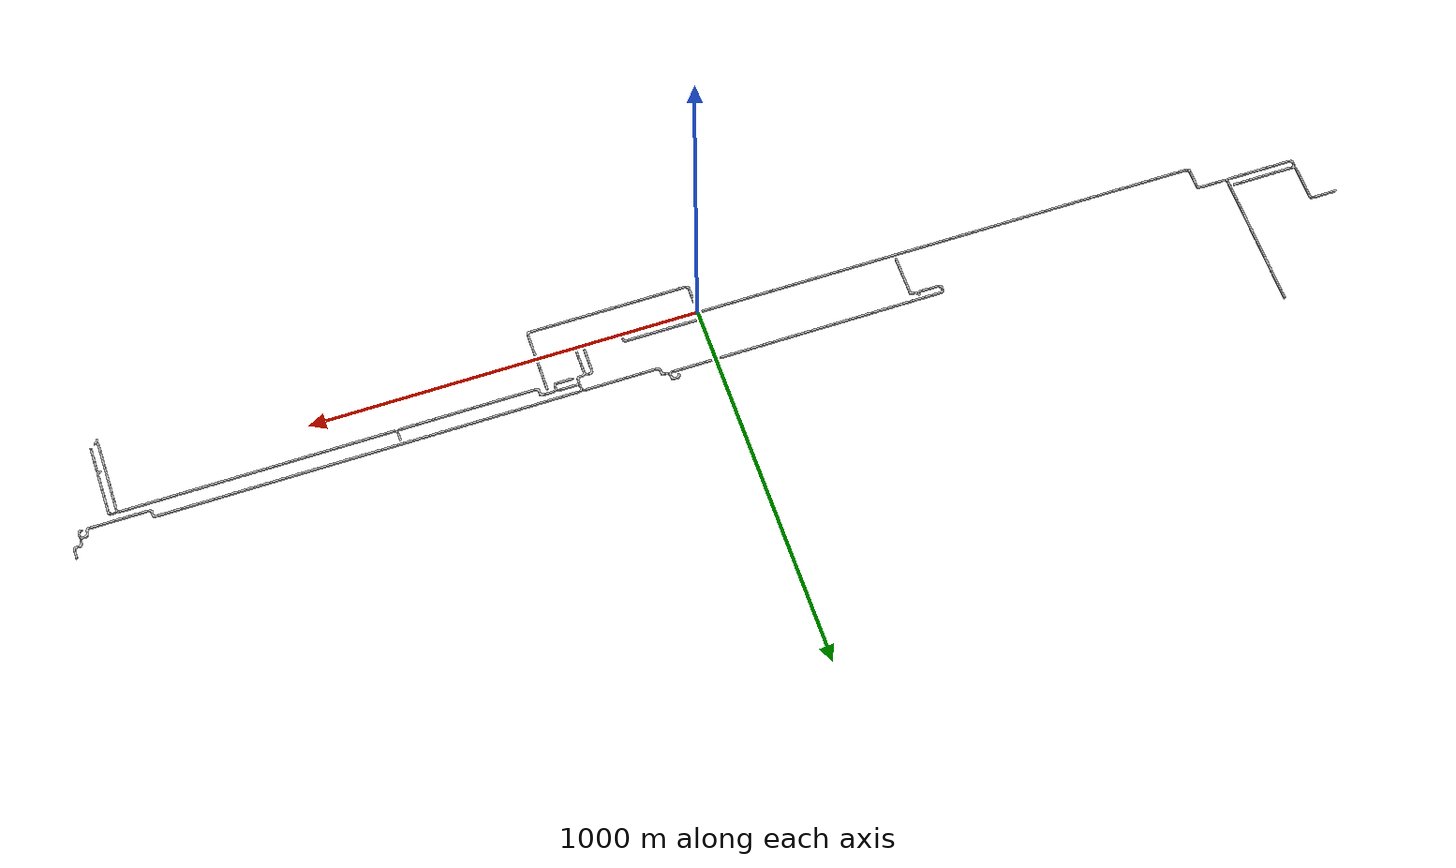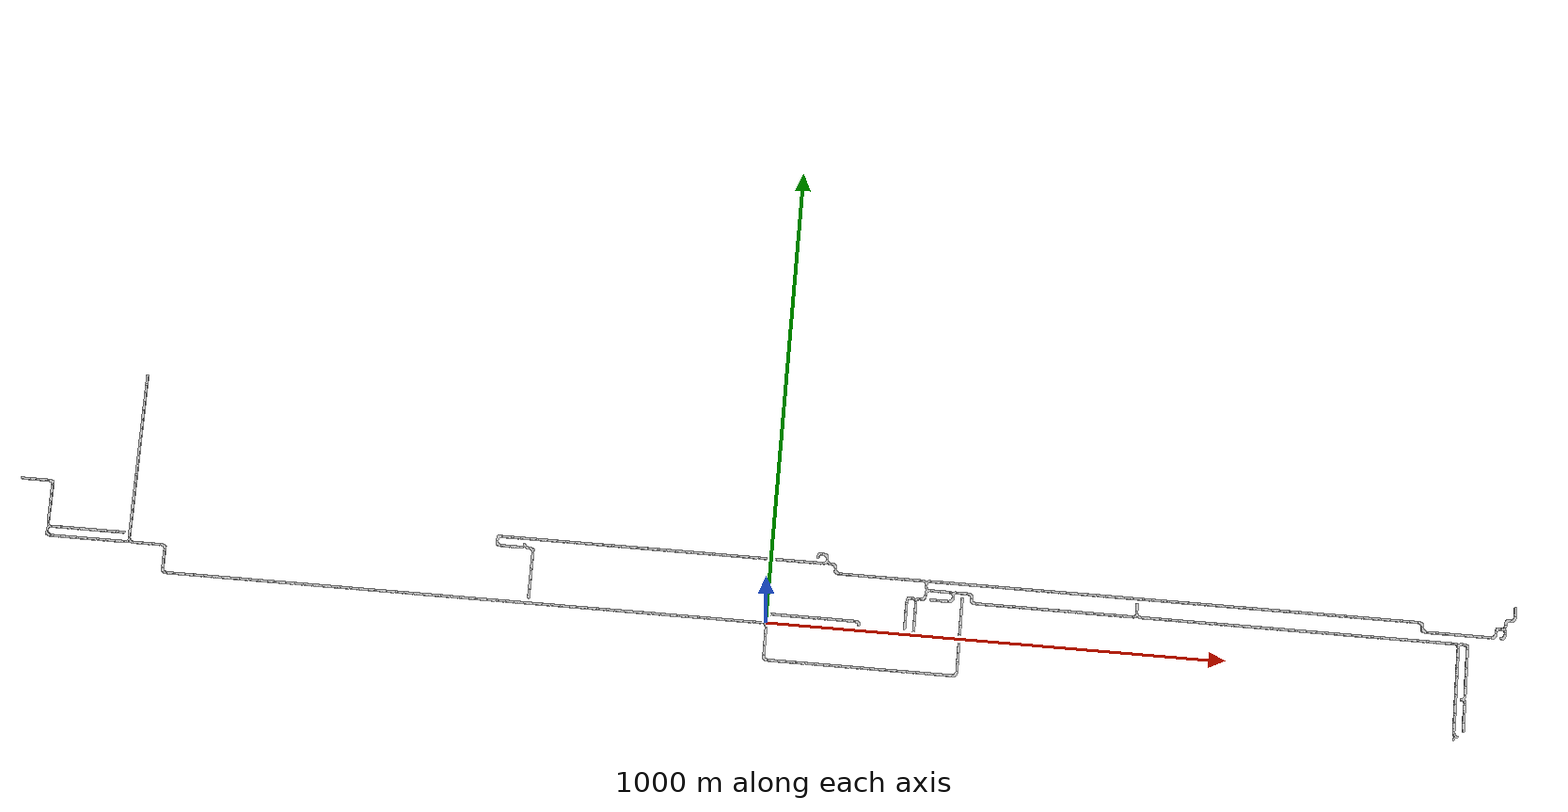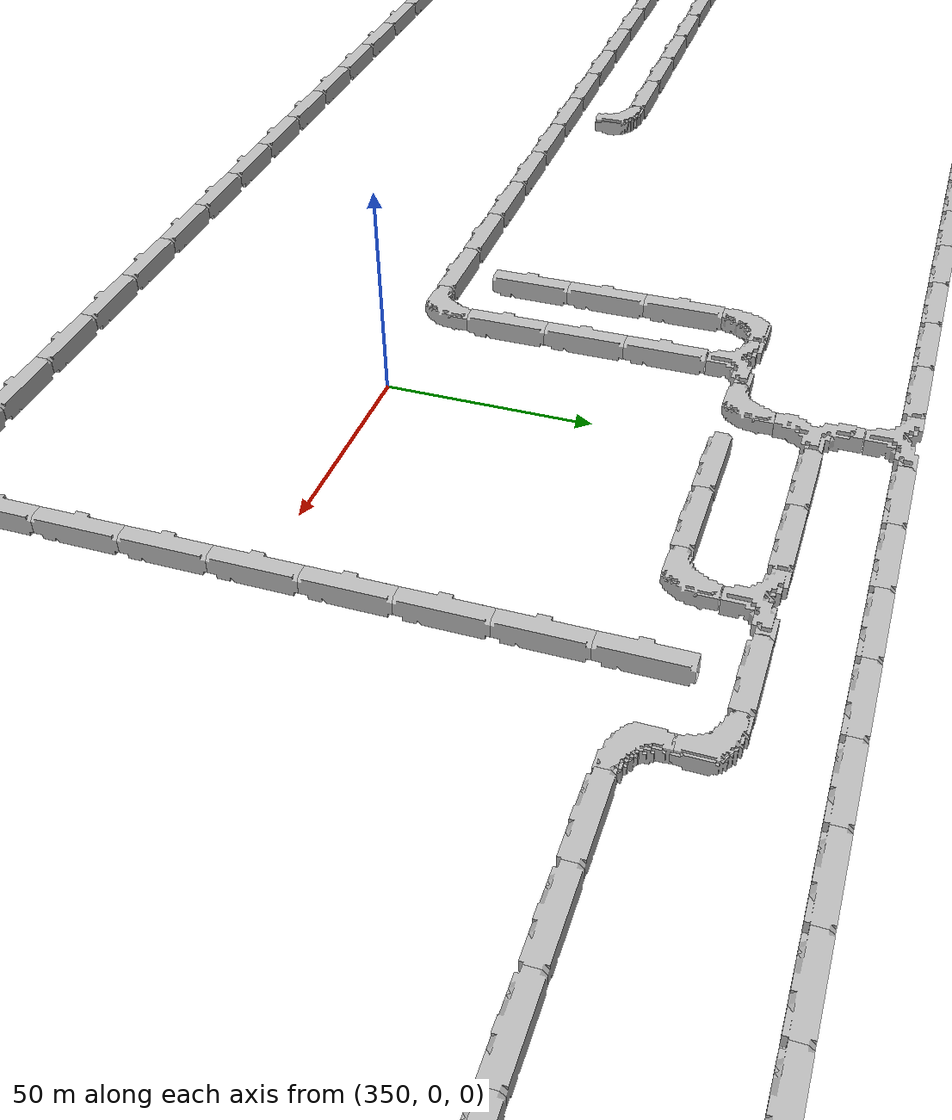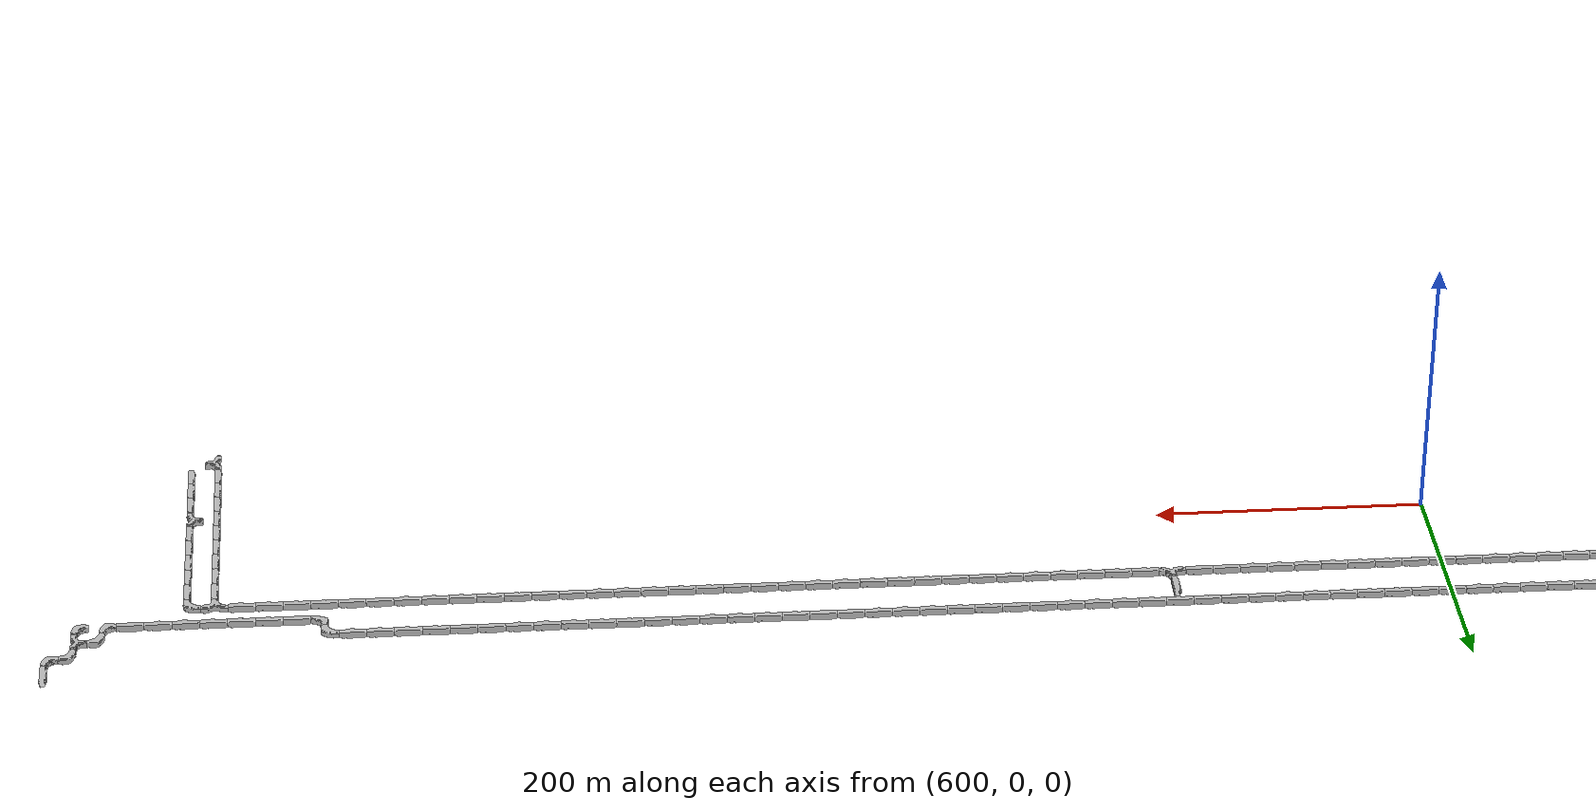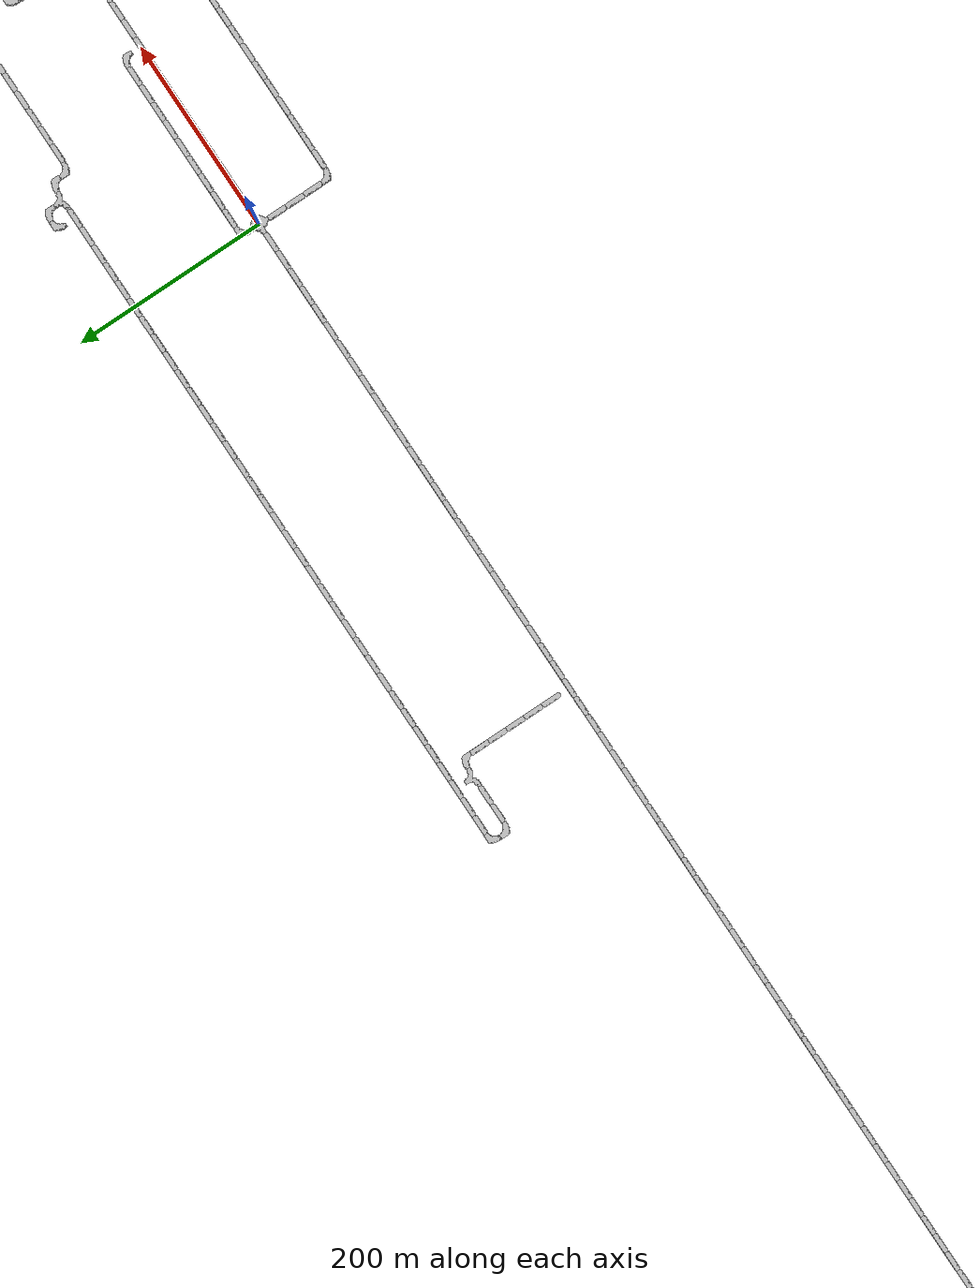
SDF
<sdf version="1.6">
 <world name="cave_8000_2">
  <include>
   <static>true</static>
   <name>cave_0_0</name>
   <pose>0 0 0 0 0 -1.5707963267948966</pose>
   <uri>model://cave_4way_20m</uri>
  </include>
  <include>
   <static>true</static>
   <name>cave_1_0</name>
   <pose>20 0 0 0 0 1.5707963267948966</pose>
   <uri>model://cave_straight_20m</uri>
  </include>
  <include>
   <static>true</static>
   <name>cave_2_0</name>
   <pose>40 0 0 0 0 1.5707963267948966</pose>
   <uri>model://cave_straight_20m</uri>
  </include>
  <include>
   <static>true</static>
   <name>cave_3_0</name>
   <pose>60 0 0 0 0 1.5707963267948966</pose>
   <uri>model://cave_straight_20m</uri>
  </include>
  <include>
   <static>true</static>
   <name>cave_4_0</name>
   <pose>80 0 0 0 0 1.5707963267948966</pose>
   <uri>model://cave_straight_20m</uri>
  </include>
  <include>
   <static>true</static>
   <name>cave_5_0</name>
   <pose>100 0 0 0 0 1.5707963267948966</pose>
   <uri>model://cave_straight_20m</uri>
  </include>
  <include>
   <static>true</static>
   <name>cave_6_0</name>
   <pose>120 0 0 0 0 1.5707963267948966</pose>
   <uri>model://cave_straight_20m</uri>
  </include>
  <include>
   <static>true</static>
   <name>cave_7_0</name>
   <pose>140 0 0 0 0 1.5707963267948966</pose>
   <uri>model://cave_straight_20m</uri>
  </include>
  <include>
   <static>true</static>
   <name>cave_8_0</name>
   <pose>160 0 0 0 0 1.5707963267948966</pose>
   <uri>model://cave_straight_20m</uri>
  </include>
  <include>
   <static>true</static>
   <name>cave_9_0</name>
   <pose>180 0 0 0 0 1.5707963267948966</pose>
   <uri>model://cave_straight_20m</uri>
  </include>
  <include>
   <static>true</static>
   <name>cave_10_0</name>
   <pose>200 0 0 0 0 1.5707963267948966</pose>
   <uri>model://cave_straight_20m</uri>
  </include>
  <include>
   <static>true</static>
   <name>cave_11_0</name>
   <pose>220 0 0 0 0 1.5707963267948966</pose>
   <uri>model://cave_straight_20m</uri>
  </include>
  <include>
   <static>true</static>
   <name>cave_12_0</name>
   <pose>240 0 0 0 0 1.5707963267948966</pose>
   <uri>model://cave_straight_20m</uri>
  </include>
  <include>
   <static>true</static>
   <name>cave_13_0</name>
   <pose>260 0 0 0 0 1.5707963267948966</pose>
   <uri>model://cave_straight_20m</uri>
  </include>
  <include>
   <static>true</static>
   <name>cave_14_0</name>
   <pose>280 0 0 0 0 1.5707963267948966</pose>
   <uri>model://cave_straight_20m</uri>
  </include>
  <include>
   <static>true</static>
   <name>cave_15_0</name>
   <pose>300 0 0 0 0 1.5707963267948966</pose>
   <uri>model://cave_straight_20m</uri>
  </include>
  <include>
   <static>true</static>
   <name>cave_16_0</name>
   <pose>320 0 0 0 0 1.5707963267948966</pose>
   <uri>model://cave_L_20m</uri>
  </include>
  <include>
   <static>true</static>
   <name>cave_16_1</name>
   <pose>320 20 0 0 0 0.0</pose>
   <uri>model://cave_straight_20m</uri>
  </include>
  <include>
   <static>true</static>
   <name>cave_16_2</name>
   <pose>320 40 0 0 0 0.0</pose>
   <uri>model://cave_straight_20m</uri>
  </include>
  <include>
   <static>true</static>
   <name>cave_16_3</name>
   <pose>320 60 0 0 0 0.0</pose>
   <uri>model://cave_straight_20m</uri>
  </include>
  <include>
   <static>true</static>
   <name>cave_16_4</name>
   <pose>320 80 0 0 0 3.141592653589793</pose>
   <uri>model://cave_3way_20m</uri>
  </include>
  <include>
   <static>true</static>
   <name>cave_17_4</name>
   <pose>340 80 0 0 0 1.5707963267948966</pose>
   <uri>model://cave_L_20m</uri>
  </include>
  <include>
   <static>true</static>
   <name>cave_17_5</name>
   <pose>340 100 0 0 0 -1.5707963267948966</pose>
   <uri>model://cave_3way_20m</uri>
  </include>
  <include>
   <static>true</static>
   <name>cave_18_5</name>
   <pose>360 100 0 0 0 1.5707963267948966</pose>
   <uri>model://cave_straight_20m</uri>
  </include>
  <include>
   <static>true</static>
   <name>cave_19_5</name>
   <pose>380 100 0 0 0 1.5707963267948966</pose>
   <uri>model://cave_straight_20m</uri>
  </include>
  <include>
   <static>true</static>
   <name>cave_20_5</name>
   <pose>400 100 0 0 0 3.141592653589793</pose>
   <uri>model://cave_3way_20m</uri>
  </include>
  <include>
   <static>true</static>
   <name>cave_21_5</name>
   <pose>420 100 0 0 0 1.5707963267948966</pose>
   <uri>model://cave_straight_20m</uri>
  </include>
  <include>
   <static>true</static>
   <name>cave_22_5</name>
   <pose>440 100 0 0 0 3.141592653589793</pose>
   <uri>model://cave_L_20m</uri>
  </include>
  <include>
   <static>true</static>
   <name>cave_22_4</name>
   <pose>440 80 0 0 0 0.0</pose>
   <uri>model://cave_L_20m</uri>
  </include>
  <include>
   <static>true</static>
   <name>cave_23_4</name>
   <pose>460 80 0 0 0 1.5707963267948966</pose>
   <uri>model://cave_straight_20m</uri>
  </include>
  <include>
   <static>true</static>
   <name>cave_24_4</name>
   <pose>480 80 0 0 0 1.5707963267948966</pose>
   <uri>model://cave_straight_20m</uri>
  </include>
  <include>
   <static>true</static>
   <name>cave_25_4</name>
   <pose>500 80 0 0 0 1.5707963267948966</pose>
   <uri>model://cave_straight_20m</uri>
  </include>
  <include>
   <static>true</static>
   <name>cave_26_4</name>
   <pose>520 80 0 0 0 1.5707963267948966</pose>
   <uri>model://cave_straight_20m</uri>
  </include>
  <include>
   <static>true</static>
   <name>cave_27_4</name>
   <pose>540 80 0 0 0 1.5707963267948966</pose>
   <uri>model://cave_straight_20m</uri>
  </include>
  <include>
   <static>true</static>
   <name>cave_28_4</name>
   <pose>560 80 0 0 0 1.5707963267948966</pose>
   <uri>model://cave_straight_20m</uri>
  </include>
  <include>
   <static>true</static>
   <name>cave_29_4</name>
   <pose>580 80 0 0 0 1.5707963267948966</pose>
   <uri>model://cave_straight_20m</uri>
  </include>
  <include>
   <static>true</static>
   <name>cave_30_4</name>
   <pose>600 80 0 0 0 1.5707963267948966</pose>
   <uri>model://cave_straight_20m</uri>
  </include>
  <include>
   <static>true</static>
   <name>cave_31_4</name>
   <pose>620 80 0 0 0 1.5707963267948966</pose>
   <uri>model://cave_straight_20m</uri>
  </include>
  <include>
   <static>true</static>
   <name>cave_32_4</name>
   <pose>640 80 0 0 0 1.5707963267948966</pose>
   <uri>model://cave_straight_20m</uri>
  </include>
  <include>
   <static>true</static>
   <name>cave_33_4</name>
   <pose>660 80 0 0 0 1.5707963267948966</pose>
   <uri>model://cave_straight_20m</uri>
  </include>
  <include>
   <static>true</static>
   <name>cave_34_4</name>
   <pose>680 80 0 0 0 1.5707963267948966</pose>
   <uri>model://cave_straight_20m</uri>
  </include>
  <include>
   <static>true</static>
   <name>cave_35_4</name>
   <pose>700 80 0 0 0 1.5707963267948966</pose>
   <uri>model://cave_straight_20m</uri>
  </include>
  <include>
   <static>true</static>
   <name>cave_36_4</name>
   <pose>720 80 0 0 0 1.5707963267948966</pose>
   <uri>model://cave_straight_20m</uri>
  </include>
  <include>
   <static>true</static>
   <name>cave_37_4</name>
   <pose>740 80 0 0 0 1.5707963267948966</pose>
   <uri>model://cave_straight_20m</uri>
  </include>
  <include>
   <static>true</static>
   <name>cave_38_4</name>
   <pose>760 80 0 0 0 1.5707963267948966</pose>
   <uri>model://cave_straight_20m</uri>
  </include>
  <include>
   <static>true</static>
   <name>cave_39_4</name>
   <pose>780 80 0 0 0 1.5707963267948966</pose>
   <uri>model://cave_straight_20m</uri>
  </include>
  <include>
   <static>true</static>
   <name>cave_40_4</name>
   <pose>800 80 0 0 0 0.0</pose>
   <uri>model://cave_3way_20m</uri>
  </include>
  <include>
   <static>true</static>
   <name>cave_41_4</name>
   <pose>820 80 0 0 0 1.5707963267948966</pose>
   <uri>model://cave_straight_20m</uri>
  </include>
  <include>
   <static>true</static>
   <name>cave_42_4</name>
   <pose>840 80 0 0 0 1.5707963267948966</pose>
   <uri>model://cave_straight_20m</uri>
  </include>
  <include>
   <static>true</static>
   <name>cave_43_4</name>
   <pose>860 80 0 0 0 1.5707963267948966</pose>
   <uri>model://cave_straight_20m</uri>
  </include>
  <include>
   <static>true</static>
   <name>cave_44_4</name>
   <pose>880 80 0 0 0 1.5707963267948966</pose>
   <uri>model://cave_straight_20m</uri>
  </include>
  <include>
   <static>true</static>
   <name>cave_45_4</name>
   <pose>900 80 0 0 0 1.5707963267948966</pose>
   <uri>model://cave_straight_20m</uri>
  </include>
  <include>
   <static>true</static>
   <name>cave_46_4</name>
   <pose>920 80 0 0 0 1.5707963267948966</pose>
   <uri>model://cave_straight_20m</uri>
  </include>
  <include>
   <static>true</static>
   <name>cave_47_4</name>
   <pose>940 80 0 0 0 1.5707963267948966</pose>
   <uri>model://cave_straight_20m</uri>
  </include>
  <include>
   <static>true</static>
   <name>cave_48_4</name>
   <pose>960 80 0 0 0 1.5707963267948966</pose>
   <uri>model://cave_straight_20m</uri>
  </include>
  <include>
   <static>true</static>
   <name>cave_49_4</name>
   <pose>980 80 0 0 0 1.5707963267948966</pose>
   <uri>model://cave_straight_20m</uri>
  </include>
  <include>
   <static>true</static>
   <name>cave_50_4</name>
   <pose>1000 80 0 0 0 1.5707963267948966</pose>
   <uri>model://cave_straight_20m</uri>
  </include>
  <include>
   <static>true</static>
   <name>cave_51_4</name>
   <pose>1020 80 0 0 0 1.5707963267948966</pose>
   <uri>model://cave_straight_20m</uri>
  </include>
  <include>
   <static>true</static>
   <name>cave_52_4</name>
   <pose>1040 80 0 0 0 1.5707963267948966</pose>
   <uri>model://cave_straight_20m</uri>
  </include>
  <include>
   <static>true</static>
   <name>cave_53_4</name>
   <pose>1060 80 0 0 0 1.5707963267948966</pose>
   <uri>model://cave_straight_20m</uri>
  </include>
  <include>
   <static>true</static>
   <name>cave_54_4</name>
   <pose>1080 80 0 0 0 1.5707963267948966</pose>
   <uri>model://cave_straight_20m</uri>
  </include>
  <include>
   <static>true</static>
   <name>cave_55_4</name>
   <pose>1100 80 0 0 0 1.5707963267948966</pose>
   <uri>model://cave_straight_20m</uri>
  </include>
  <include>
   <static>true</static>
   <name>cave_56_4</name>
   <pose>1120 80 0 0 0 1.5707963267948966</pose>
   <uri>model://cave_straight_20m</uri>
  </include>
  <include>
   <static>true</static>
   <name>cave_57_4</name>
   <pose>1140 80 0 0 0 1.5707963267948966</pose>
   <uri>model://cave_straight_20m</uri>
  </include>
  <include>
   <static>true</static>
   <name>cave_58_4</name>
   <pose>1160 80 0 0 0 1.5707963267948966</pose>
   <uri>model://cave_straight_20m</uri>
  </include>
  <include>
   <static>true</static>
   <name>cave_59_4</name>
   <pose>1180 80 0 0 0 1.5707963267948966</pose>
   <uri>model://cave_straight_20m</uri>
  </include>
  <include>
   <static>true</static>
   <name>cave_60_4</name>
   <pose>1200 80 0 0 0 1.5707963267948966</pose>
   <uri>model://cave_straight_20m</uri>
  </include>
  <include>
   <static>true</static>
   <name>cave_61_4</name>
   <pose>1220 80 0 0 0 1.5707963267948966</pose>
   <uri>model://cave_straight_20m</uri>
  </include>
  <include>
   <static>true</static>
   <name>cave_62_4</name>
   <pose>1240 80 0 0 0 1.5707963267948966</pose>
   <uri>model://cave_straight_20m</uri>
  </include>
  <include>
   <static>true</static>
   <name>cave_63_4</name>
   <pose>1260 80 0 0 0 1.5707963267948966</pose>
   <uri>model://cave_straight_20m</uri>
  </include>
  <include>
   <static>true</static>
   <name>cave_64_4</name>
   <pose>1280 80 0 0 0 1.5707963267948966</pose>
   <uri>model://cave_straight_20m</uri>
  </include>
  <include>
   <static>true</static>
   <name>cave_65_4</name>
   <pose>1300 80 0 0 0 1.5707963267948966</pose>
   <uri>model://cave_straight_20m</uri>
  </include>
  <include>
   <static>true</static>
   <name>cave_66_4</name>
   <pose>1320 80 0 0 0 1.5707963267948966</pose>
   <uri>model://cave_straight_20m</uri>
  </include>
  <include>
   <static>true</static>
   <name>cave_67_4</name>
   <pose>1340 80 0 0 0 1.5707963267948966</pose>
   <uri>model://cave_straight_20m</uri>
  </include>
  <include>
   <static>true</static>
   <name>cave_68_4</name>
   <pose>1360 80 0 0 0 1.5707963267948966</pose>
   <uri>model://cave_straight_20m</uri>
  </include>
  <include>
   <static>true</static>
   <name>cave_69_4</name>
   <pose>1380 80 0 0 0 1.5707963267948966</pose>
   <uri>model://cave_straight_20m</uri>
  </include>
  <include>
   <static>true</static>
   <name>cave_70_4</name>
   <pose>1400 80 0 0 0 1.5707963267948966</pose>
   <uri>model://cave_straight_20m</uri>
  </include>
  <include>
   <static>true</static>
   <name>cave_71_4</name>
   <pose>1420 80 0 0 0 1.5707963267948966</pose>
   <uri>model://cave_straight_20m</uri>
  </include>
  <include>
   <static>true</static>
   <name>cave_72_4</name>
   <pose>1440 80 0 0 0 1.5707963267948966</pose>
   <uri>model://cave_straight_20m</uri>
  </include>
  <include>
   <static>true</static>
   <name>cave_73_4</name>
   <pose>1460 80 0 0 0 1.5707963267948966</pose>
   <uri>model://cave_straight_20m</uri>
  </include>
  <include>
   <static>true</static>
   <name>cave_74_4</name>
   <pose>1480 80 0 0 0 1.5707963267948966</pose>
   <uri>model://cave_straight_20m</uri>
  </include>
  <include>
   <static>true</static>
   <name>cave_75_4</name>
   <pose>1500 80 0 0 0 3.141592653589793</pose>
   <uri>model://cave_3way_20m</uri>
  </include>
  <include>
   <static>true</static>
   <name>cave_76_4</name>
   <pose>1520 80 0 0 0 3.141592653589793</pose>
   <uri>model://cave_L_20m</uri>
  </include>
  <include>
   <static>true</static>
   <name>cave_76_3</name>
   <pose>1520 60 0 0 0 0.0</pose>
   <uri>model://cave_straight_20m</uri>
  </include>
  <include>
   <static>true</static>
   <name>cave_76_2</name>
   <pose>1520 40 0 0 0 0.0</pose>
   <uri>model://cave_straight_20m</uri>
  </include>
  <include>
   <static>true</static>
   <name>cave_76_1</name>
   <pose>1520 20 0 0 0 0.0</pose>
   <uri>model://cave_straight_20m</uri>
  </include>
  <include>
   <static>true</static>
   <name>cave_76_0</name>
   <pose>1520 0 0 0 0 0.0</pose>
   <uri>model://cave_straight_20m</uri>
  </include>
  <include>
   <static>true</static>
   <name>cave_76_-1</name>
   <pose>1520 -20 0 0 0 0.0</pose>
   <uri>model://cave_straight_20m</uri>
  </include>
  <include>
   <static>true</static>
   <name>cave_76_-2</name>
   <pose>1520 -40 0 0 0 1.5707963267948966</pose>
   <uri>model://cave_3way_20m</uri>
  </include>
  <include>
   <static>true</static>
   <name>cave_76_-3</name>
   <pose>1520 -60 0 0 0 0.0</pose>
   <uri>model://cave_straight_20m</uri>
  </include>
  <include>
   <static>true</static>
   <name>cave_76_-4</name>
   <pose>1520 -80 0 0 0 0.0</pose>
   <uri>model://cave_straight_20m</uri>
  </include>
  <include>
   <static>true</static>
   <name>cave_76_-5</name>
   <pose>1520 -100 0 0 0 0.0</pose>
   <uri>model://cave_straight_20m</uri>
  </include>
  <include>
   <static>true</static>
   <name>cave_75_3</name>
   <pose>1500 60 0 0 0 0.0</pose>
   <uri>model://cave_straight_20m</uri>
  </include>
  <include>
   <static>true</static>
   <name>cave_75_2</name>
   <pose>1500 40 0 0 0 0.0</pose>
   <uri>model://cave_straight_20m</uri>
  </include>
  <include>
   <static>true</static>
   <name>cave_75_1</name>
   <pose>1500 20 0 0 0 0.0</pose>
   <uri>model://cave_straight_20m</uri>
  </include>
  <include>
   <static>true</static>
   <name>cave_75_0</name>
   <pose>1500 0 0 0 0 0.0</pose>
   <uri>model://cave_straight_20m</uri>
  </include>
  <include>
   <static>true</static>
   <name>cave_75_-1</name>
   <pose>1500 -20 0 0 0 0.0</pose>
   <uri>model://cave_straight_20m</uri>
  </include>
  <include>
   <static>true</static>
   <name>cave_75_-2</name>
   <pose>1500 -40 0 0 0 0.0</pose>
   <uri>model://cave_straight_20m</uri>
  </include>
  <include>
   <static>true</static>
   <name>cave_75_-3</name>
   <pose>1500 -60 0 0 0 0.0</pose>
   <uri>model://cave_straight_20m</uri>
  </include>
  <include>
   <static>true</static>
   <name>cave_75_-4</name>
   <pose>1500 -80 0 0 0 0.0</pose>
   <uri>model://cave_straight_20m</uri>
  </include>
  <include>
   <static>true</static>
   <name>cave_75_-5</name>
   <pose>1500 -100 0 0 0 0.0</pose>
   <uri>model://cave_straight_20m</uri>
  </include>
  <include>
   <static>true</static>
   <name>cave_75_-6</name>
   <pose>1500 -120 0 0 0 -1.5707963267948966</pose>
   <uri>model://cave_3way_20m</uri>
  </include>
  <include>
   <static>true</static>
   <name>cave_40_5</name>
   <pose>800 100 0 0 0 0.0</pose>
   <uri>model://cave_straight_20m</uri>
  </include>
  <include>
   <static>true</static>
   <name>cave_20_4</name>
   <pose>400 80 0 0 0 1.5707963267948966</pose>
   <uri>model://cave_L_20m</uri>
  </include>
  <include>
   <static>true</static>
   <name>cave_19_4</name>
   <pose>380 80 0 0 0 1.5707963267948966</pose>
   <uri>model://cave_straight_20m</uri>
  </include>
  <include>
   <static>true</static>
   <name>cave_18_4</name>
   <pose>360 80 0 0 0 1.5707963267948966</pose>
   <uri>model://cave_straight_20m</uri>
  </include>
  <include>
   <static>true</static>
   <name>cave_17_6</name>
   <pose>340 120 0 0 0 3.141592653589793</pose>
   <uri>model://cave_3way_20m</uri>
  </include>
  <include>
   <static>true</static>
   <name>cave_18_6</name>
   <pose>360 120 0 0 0 1.5707963267948966</pose>
   <uri>model://cave_straight_20m</uri>
  </include>
  <include>
   <static>true</static>
   <name>cave_19_6</name>
   <pose>380 120 0 0 0 1.5707963267948966</pose>
   <uri>model://cave_straight_20m</uri>
  </include>
  <include>
   <static>true</static>
   <name>cave_20_6</name>
   <pose>400 120 0 0 0 1.5707963267948966</pose>
   <uri>model://cave_straight_20m</uri>
  </include>
  <include>
   <static>true</static>
   <name>cave_21_6</name>
   <pose>420 120 0 0 0 1.5707963267948966</pose>
   <uri>model://cave_straight_20m</uri>
  </include>
  <include>
   <static>true</static>
   <name>cave_22_6</name>
   <pose>440 120 0 0 0 1.5707963267948966</pose>
   <uri>model://cave_straight_20m</uri>
  </include>
  <include>
   <static>true</static>
   <name>cave_23_6</name>
   <pose>460 120 0 0 0 1.5707963267948966</pose>
   <uri>model://cave_straight_20m</uri>
  </include>
  <include>
   <static>true</static>
   <name>cave_24_6</name>
   <pose>480 120 0 0 0 1.5707963267948966</pose>
   <uri>model://cave_straight_20m</uri>
  </include>
  <include>
   <static>true</static>
   <name>cave_25_6</name>
   <pose>500 120 0 0 0 1.5707963267948966</pose>
   <uri>model://cave_straight_20m</uri>
  </include>
  <include>
   <static>true</static>
   <name>cave_26_6</name>
   <pose>520 120 0 0 0 1.5707963267948966</pose>
   <uri>model://cave_straight_20m</uri>
  </include>
  <include>
   <static>true</static>
   <name>cave_27_6</name>
   <pose>540 120 0 0 0 1.5707963267948966</pose>
   <uri>model://cave_straight_20m</uri>
  </include>
  <include>
   <static>true</static>
   <name>cave_28_6</name>
   <pose>560 120 0 0 0 1.5707963267948966</pose>
   <uri>model://cave_straight_20m</uri>
  </include>
  <include>
   <static>true</static>
   <name>cave_29_6</name>
   <pose>580 120 0 0 0 1.5707963267948966</pose>
   <uri>model://cave_straight_20m</uri>
  </include>
  <include>
   <static>true</static>
   <name>cave_30_6</name>
   <pose>600 120 0 0 0 1.5707963267948966</pose>
   <uri>model://cave_straight_20m</uri>
  </include>
  <include>
   <static>true</static>
   <name>cave_31_6</name>
   <pose>620 120 0 0 0 1.5707963267948966</pose>
   <uri>model://cave_straight_20m</uri>
  </include>
  <include>
   <static>true</static>
   <name>cave_32_6</name>
   <pose>640 120 0 0 0 1.5707963267948966</pose>
   <uri>model://cave_straight_20m</uri>
  </include>
  <include>
   <static>true</static>
   <name>cave_33_6</name>
   <pose>660 120 0 0 0 1.5707963267948966</pose>
   <uri>model://cave_straight_20m</uri>
  </include>
  <include>
   <static>true</static>
   <name>cave_34_6</name>
   <pose>680 120 0 0 0 1.5707963267948966</pose>
   <uri>model://cave_straight_20m</uri>
  </include>
  <include>
   <static>true</static>
   <name>cave_35_6</name>
   <pose>700 120 0 0 0 1.5707963267948966</pose>
   <uri>model://cave_straight_20m</uri>
  </include>
  <include>
   <static>true</static>
   <name>cave_36_6</name>
   <pose>720 120 0 0 0 1.5707963267948966</pose>
   <uri>model://cave_straight_20m</uri>
  </include>
  <include>
   <static>true</static>
   <name>cave_37_6</name>
   <pose>740 120 0 0 0 1.5707963267948966</pose>
   <uri>model://cave_straight_20m</uri>
  </include>
  <include>
   <static>true</static>
   <name>cave_38_6</name>
   <pose>760 120 0 0 0 1.5707963267948966</pose>
   <uri>model://cave_straight_20m</uri>
  </include>
  <include>
   <static>true</static>
   <name>cave_39_6</name>
   <pose>780 120 0 0 0 1.5707963267948966</pose>
   <uri>model://cave_straight_20m</uri>
  </include>
  <include>
   <static>true</static>
   <name>cave_40_6</name>
   <pose>800 120 0 0 0 1.5707963267948966</pose>
   <uri>model://cave_straight_20m</uri>
  </include>
  <include>
   <static>true</static>
   <name>cave_41_6</name>
   <pose>820 120 0 0 0 1.5707963267948966</pose>
   <uri>model://cave_straight_20m</uri>
  </include>
  <include>
   <static>true</static>
   <name>cave_42_6</name>
   <pose>840 120 0 0 0 1.5707963267948966</pose>
   <uri>model://cave_straight_20m</uri>
  </include>
  <include>
   <static>true</static>
   <name>cave_43_6</name>
   <pose>860 120 0 0 0 1.5707963267948966</pose>
   <uri>model://cave_straight_20m</uri>
  </include>
  <include>
   <static>true</static>
   <name>cave_44_6</name>
   <pose>880 120 0 0 0 1.5707963267948966</pose>
   <uri>model://cave_straight_20m</uri>
  </include>
  <include>
   <static>true</static>
   <name>cave_45_6</name>
   <pose>900 120 0 0 0 1.5707963267948966</pose>
   <uri>model://cave_straight_20m</uri>
  </include>
  <include>
   <static>true</static>
   <name>cave_46_6</name>
   <pose>920 120 0 0 0 1.5707963267948966</pose>
   <uri>model://cave_straight_20m</uri>
  </include>
  <include>
   <static>true</static>
   <name>cave_47_6</name>
   <pose>940 120 0 0 0 1.5707963267948966</pose>
   <uri>model://cave_straight_20m</uri>
  </include>
  <include>
   <static>true</static>
   <name>cave_48_6</name>
   <pose>960 120 0 0 0 1.5707963267948966</pose>
   <uri>model://cave_straight_20m</uri>
  </include>
  <include>
   <static>true</static>
   <name>cave_49_6</name>
   <pose>980 120 0 0 0 1.5707963267948966</pose>
   <uri>model://cave_straight_20m</uri>
  </include>
  <include>
   <static>true</static>
   <name>cave_50_6</name>
   <pose>1000 120 0 0 0 1.5707963267948966</pose>
   <uri>model://cave_straight_20m</uri>
  </include>
  <include>
   <static>true</static>
   <name>cave_51_6</name>
   <pose>1020 120 0 0 0 1.5707963267948966</pose>
   <uri>model://cave_straight_20m</uri>
  </include>
  <include>
   <static>true</static>
   <name>cave_52_6</name>
   <pose>1040 120 0 0 0 1.5707963267948966</pose>
   <uri>model://cave_straight_20m</uri>
  </include>
  <include>
   <static>true</static>
   <name>cave_53_6</name>
   <pose>1060 120 0 0 0 1.5707963267948966</pose>
   <uri>model://cave_straight_20m</uri>
  </include>
  <include>
   <static>true</static>
   <name>cave_54_6</name>
   <pose>1080 120 0 0 0 1.5707963267948966</pose>
   <uri>model://cave_straight_20m</uri>
  </include>
  <include>
   <static>true</static>
   <name>cave_55_6</name>
   <pose>1100 120 0 0 0 1.5707963267948966</pose>
   <uri>model://cave_straight_20m</uri>
  </include>
  <include>
   <static>true</static>
   <name>cave_56_6</name>
   <pose>1120 120 0 0 0 1.5707963267948966</pose>
   <uri>model://cave_straight_20m</uri>
  </include>
  <include>
   <static>true</static>
   <name>cave_57_6</name>
   <pose>1140 120 0 0 0 1.5707963267948966</pose>
   <uri>model://cave_straight_20m</uri>
  </include>
  <include>
   <static>true</static>
   <name>cave_58_6</name>
   <pose>1160 120 0 0 0 1.5707963267948966</pose>
   <uri>model://cave_straight_20m</uri>
  </include>
  <include>
   <static>true</static>
   <name>cave_59_6</name>
   <pose>1180 120 0 0 0 1.5707963267948966</pose>
   <uri>model://cave_straight_20m</uri>
  </include>
  <include>
   <static>true</static>
   <name>cave_60_6</name>
   <pose>1200 120 0 0 0 1.5707963267948966</pose>
   <uri>model://cave_straight_20m</uri>
  </include>
  <include>
   <static>true</static>
   <name>cave_61_6</name>
   <pose>1220 120 0 0 0 1.5707963267948966</pose>
   <uri>model://cave_straight_20m</uri>
  </include>
  <include>
   <static>true</static>
   <name>cave_62_6</name>
   <pose>1240 120 0 0 0 1.5707963267948966</pose>
   <uri>model://cave_straight_20m</uri>
  </include>
  <include>
   <static>true</static>
   <name>cave_63_6</name>
   <pose>1260 120 0 0 0 1.5707963267948966</pose>
   <uri>model://cave_straight_20m</uri>
  </include>
  <include>
   <static>true</static>
   <name>cave_64_6</name>
   <pose>1280 120 0 0 0 1.5707963267948966</pose>
   <uri>model://cave_straight_20m</uri>
  </include>
  <include>
   <static>true</static>
   <name>cave_65_6</name>
   <pose>1300 120 0 0 0 1.5707963267948966</pose>
   <uri>model://cave_straight_20m</uri>
  </include>
  <include>
   <static>true</static>
   <name>cave_66_6</name>
   <pose>1320 120 0 0 0 1.5707963267948966</pose>
   <uri>model://cave_straight_20m</uri>
  </include>
  <include>
   <static>true</static>
   <name>cave_67_6</name>
   <pose>1340 120 0 0 0 1.5707963267948966</pose>
   <uri>model://cave_straight_20m</uri>
  </include>
  <include>
   <static>true</static>
   <name>cave_68_6</name>
   <pose>1360 120 0 0 0 1.5707963267948966</pose>
   <uri>model://cave_straight_20m</uri>
  </include>
  <include>
   <static>true</static>
   <name>cave_69_6</name>
   <pose>1380 120 0 0 0 1.5707963267948966</pose>
   <uri>model://cave_straight_20m</uri>
  </include>
  <include>
   <static>true</static>
   <name>cave_70_6</name>
   <pose>1400 120 0 0 0 1.5707963267948966</pose>
   <uri>model://cave_straight_20m</uri>
  </include>
  <include>
   <static>true</static>
   <name>cave_71_6</name>
   <pose>1420 120 0 0 0 3.141592653589793</pose>
   <uri>model://cave_L_20m</uri>
  </include>
  <include>
   <static>true</static>
   <name>cave_71_5</name>
   <pose>1420 100 0 0 0 0.0</pose>
   <uri>model://cave_L_20m</uri>
  </include>
  <include>
   <static>true</static>
   <name>cave_72_5</name>
   <pose>1440 100 0 0 0 1.5707963267948966</pose>
   <uri>model://cave_straight_20m</uri>
  </include>
  <include>
   <static>true</static>
   <name>cave_73_5</name>
   <pose>1460 100 0 0 0 1.5707963267948966</pose>
   <uri>model://cave_straight_20m</uri>
  </include>
  <include>
   <static>true</static>
   <name>cave_74_5</name>
   <pose>1480 100 0 0 0 1.5707963267948966</pose>
   <uri>model://cave_straight_20m</uri>
  </include>
  <include>
   <static>true</static>
   <name>cave_75_5</name>
   <pose>1500 100 0 0 0 1.5707963267948966</pose>
   <uri>model://cave_straight_20m</uri>
  </include>
  <include>
   <static>true</static>
   <name>cave_76_5</name>
   <pose>1520 100 0 0 0 1.5707963267948966</pose>
   <uri>model://cave_straight_20m</uri>
  </include>
  <include>
   <static>true</static>
   <name>cave_77_5</name>
   <pose>1540 100 0 0 0 1.5707963267948966</pose>
   <uri>model://cave_straight_20m</uri>
  </include>
  <include>
   <static>true</static>
   <name>cave_78_5</name>
   <pose>1560 100 0 0 0 1.5707963267948966</pose>
   <uri>model://cave_straight_20m</uri>
  </include>
  <include>
   <static>true</static>
   <name>cave_79_5</name>
   <pose>1580 100 0 0 0 1.5707963267948966</pose>
   <uri>model://cave_L_20m</uri>
  </include>
  <include>
   <static>true</static>
   <name>cave_79_6</name>
   <pose>1580 120 0 0 0 -1.5707963267948966</pose>
   <uri>model://cave_L_20m</uri>
  </include>
  <include>
   <static>true</static>
   <name>cave_80_6</name>
   <pose>1600 120 0 0 0 1.5707963267948966</pose>
   <uri>model://cave_3way_20m</uri>
  </include>
  <include>
   <static>true</static>
   <name>cave_80_5</name>
   <pose>1600 100 0 0 0 1.5707963267948966</pose>
   <uri>model://cave_L_20m</uri>
  </include>
  <include>
   <static>true</static>
   <name>cave_80_7</name>
   <pose>1600 140 0 0 0 -1.5707963267948966</pose>
   <uri>model://cave_L_20m</uri>
  </include>
  <include>
   <static>true</static>
   <name>cave_81_7</name>
   <pose>1620 140 0 0 0 1.5707963267948966</pose>
   <uri>model://cave_L_20m</uri>
  </include>
  <include>
   <static>true</static>
   <name>cave_81_8</name>
   <pose>1620 160 0 0 0 0.0</pose>
   <uri>model://cave_straight_20m</uri>
  </include>
  <include>
   <static>true</static>
   <name>cave_16_6</name>
   <pose>320 120 0 0 0 1.5707963267948966</pose>
   <uri>model://cave_straight_20m</uri>
  </include>
  <include>
   <static>true</static>
   <name>cave_15_6</name>
   <pose>300 120 0 0 0 1.5707963267948966</pose>
   <uri>model://cave_straight_20m</uri>
  </include>
  <include>
   <static>true</static>
   <name>cave_14_6</name>
   <pose>280 120 0 0 0 1.5707963267948966</pose>
   <uri>model://cave_straight_20m</uri>
  </include>
  <include>
   <static>true</static>
   <name>cave_13_6</name>
   <pose>260 120 0 0 0 1.5707963267948966</pose>
   <uri>model://cave_straight_20m</uri>
  </include>
  <include>
   <static>true</static>
   <name>cave_12_6</name>
   <pose>240 120 0 0 0 1.5707963267948966</pose>
   <uri>model://cave_straight_20m</uri>
  </include>
  <include>
   <static>true</static>
   <name>cave_11_6</name>
   <pose>220 120 0 0 0 1.5707963267948966</pose>
   <uri>model://cave_straight_20m</uri>
  </include>
  <include>
   <static>true</static>
   <name>cave_10_6</name>
   <pose>200 120 0 0 0 1.5707963267948966</pose>
   <uri>model://cave_straight_20m</uri>
  </include>
  <include>
   <static>true</static>
   <name>cave_9_6</name>
   <pose>180 120 0 0 0 1.5707963267948966</pose>
   <uri>model://cave_straight_20m</uri>
  </include>
  <include>
   <static>true</static>
   <name>cave_8_6</name>
   <pose>160 120 0 0 0 1.5707963267948966</pose>
   <uri>model://cave_straight_20m</uri>
  </include>
  <include>
   <static>true</static>
   <name>cave_7_6</name>
   <pose>140 120 0 0 0 0.0</pose>
   <uri>model://cave_L_20m</uri>
  </include>
  <include>
   <static>true</static>
   <name>cave_7_7</name>
   <pose>140 140 0 0 0 3.141592653589793</pose>
   <uri>model://cave_L_20m</uri>
  </include>
  <include>
   <static>true</static>
   <name>cave_6_7</name>
   <pose>120 140 0 0 0 0.0</pose>
   <uri>model://cave_3way_20m</uri>
  </include>
  <include>
   <static>true</static>
   <name>cave_5_7</name>
   <pose>100 140 0 0 0 1.5707963267948966</pose>
   <uri>model://cave_straight_20m</uri>
  </include>
  <include>
   <static>true</static>
   <name>cave_4_7</name>
   <pose>80 140 0 0 0 1.5707963267948966</pose>
   <uri>model://cave_straight_20m</uri>
  </include>
  <include>
   <static>true</static>
   <name>cave_3_7</name>
   <pose>60 140 0 0 0 1.5707963267948966</pose>
   <uri>model://cave_straight_20m</uri>
  </include>
  <include>
   <static>true</static>
   <name>cave_2_7</name>
   <pose>40 140 0 0 0 1.5707963267948966</pose>
   <uri>model://cave_straight_20m</uri>
  </include>
  <include>
   <static>true</static>
   <name>cave_1_7</name>
   <pose>20 140 0 0 0 1.5707963267948966</pose>
   <uri>model://cave_straight_20m</uri>
  </include>
  <include>
   <static>true</static>
   <name>cave_0_7</name>
   <pose>0 140 0 0 0 1.5707963267948966</pose>
   <uri>model://cave_straight_20m</uri>
  </include>
  <include>
   <static>true</static>
   <name>cave_-1_7</name>
   <pose>-20 140 0 0 0 1.5707963267948966</pose>
   <uri>model://cave_straight_20m</uri>
  </include>
  <include>
   <static>true</static>
   <name>cave_-2_7</name>
   <pose>-40 140 0 0 0 1.5707963267948966</pose>
   <uri>model://cave_straight_20m</uri>
  </include>
  <include>
   <static>true</static>
   <name>cave_-3_7</name>
   <pose>-60 140 0 0 0 1.5707963267948966</pose>
   <uri>model://cave_straight_20m</uri>
  </include>
  <include>
   <static>true</static>
   <name>cave_-4_7</name>
   <pose>-80 140 0 0 0 1.5707963267948966</pose>
   <uri>model://cave_straight_20m</uri>
  </include>
  <include>
   <static>true</static>
   <name>cave_-5_7</name>
   <pose>-100 140 0 0 0 1.5707963267948966</pose>
   <uri>model://cave_straight_20m</uri>
  </include>
  <include>
   <static>true</static>
   <name>cave_-6_7</name>
   <pose>-120 140 0 0 0 1.5707963267948966</pose>
   <uri>model://cave_straight_20m</uri>
  </include>
  <include>
   <static>true</static>
   <name>cave_-7_7</name>
   <pose>-140 140 0 0 0 1.5707963267948966</pose>
   <uri>model://cave_straight_20m</uri>
  </include>
  <include>
   <static>true</static>
   <name>cave_-8_7</name>
   <pose>-160 140 0 0 0 1.5707963267948966</pose>
   <uri>model://cave_straight_20m</uri>
  </include>
  <include>
   <static>true</static>
   <name>cave_-9_7</name>
   <pose>-180 140 0 0 0 1.5707963267948966</pose>
   <uri>model://cave_straight_20m</uri>
  </include>
  <include>
   <static>true</static>
   <name>cave_-10_7</name>
   <pose>-200 140 0 0 0 1.5707963267948966</pose>
   <uri>model://cave_straight_20m</uri>
  </include>
  <include>
   <static>true</static>
   <name>cave_-11_7</name>
   <pose>-220 140 0 0 0 1.5707963267948966</pose>
   <uri>model://cave_straight_20m</uri>
  </include>
  <include>
   <static>true</static>
   <name>cave_-12_7</name>
   <pose>-240 140 0 0 0 1.5707963267948966</pose>
   <uri>model://cave_straight_20m</uri>
  </include>
  <include>
   <static>true</static>
   <name>cave_-13_7</name>
   <pose>-260 140 0 0 0 1.5707963267948966</pose>
   <uri>model://cave_straight_20m</uri>
  </include>
  <include>
   <static>true</static>
   <name>cave_-14_7</name>
   <pose>-280 140 0 0 0 1.5707963267948966</pose>
   <uri>model://cave_straight_20m</uri>
  </include>
  <include>
   <static>true</static>
   <name>cave_-15_7</name>
   <pose>-300 140 0 0 0 1.5707963267948966</pose>
   <uri>model://cave_straight_20m</uri>
  </include>
  <include>
   <static>true</static>
   <name>cave_-16_7</name>
   <pose>-320 140 0 0 0 1.5707963267948966</pose>
   <uri>model://cave_straight_20m</uri>
  </include>
  <include>
   <static>true</static>
   <name>cave_-17_7</name>
   <pose>-340 140 0 0 0 1.5707963267948966</pose>
   <uri>model://cave_straight_20m</uri>
  </include>
  <include>
   <static>true</static>
   <name>cave_-18_7</name>
   <pose>-360 140 0 0 0 1.5707963267948966</pose>
   <uri>model://cave_straight_20m</uri>
  </include>
  <include>
   <static>true</static>
   <name>cave_-19_7</name>
   <pose>-380 140 0 0 0 1.5707963267948966</pose>
   <uri>model://cave_straight_20m</uri>
  </include>
  <include>
   <static>true</static>
   <name>cave_-20_7</name>
   <pose>-400 140 0 0 0 1.5707963267948966</pose>
   <uri>model://cave_straight_20m</uri>
  </include>
  <include>
   <static>true</static>
   <name>cave_-21_7</name>
   <pose>-420 140 0 0 0 1.5707963267948966</pose>
   <uri>model://cave_straight_20m</uri>
  </include>
  <include>
   <static>true</static>
   <name>cave_-22_7</name>
   <pose>-440 140 0 0 0 1.5707963267948966</pose>
   <uri>model://cave_straight_20m</uri>
  </include>
  <include>
   <static>true</static>
   <name>cave_-23_7</name>
   <pose>-460 140 0 0 0 1.5707963267948966</pose>
   <uri>model://cave_straight_20m</uri>
  </include>
  <include>
   <static>true</static>
   <name>cave_-24_7</name>
   <pose>-480 140 0 0 0 1.5707963267948966</pose>
   <uri>model://cave_straight_20m</uri>
  </include>
  <include>
   <static>true</static>
   <name>cave_-25_7</name>
   <pose>-500 140 0 0 0 1.5707963267948966</pose>
   <uri>model://cave_straight_20m</uri>
  </include>
  <include>
   <static>true</static>
   <name>cave_-26_7</name>
   <pose>-520 140 0 0 0 1.5707963267948966</pose>
   <uri>model://cave_straight_20m</uri>
  </include>
  <include>
   <static>true</static>
   <name>cave_-27_7</name>
   <pose>-540 140 0 0 0 1.5707963267948966</pose>
   <uri>model://cave_straight_20m</uri>
  </include>
  <include>
   <static>true</static>
   <name>cave_-28_7</name>
   <pose>-560 140 0 0 0 1.5707963267948966</pose>
   <uri>model://cave_straight_20m</uri>
  </include>
  <include>
   <static>true</static>
   <name>cave_-29_7</name>
   <pose>-580 140 0 0 0 1.5707963267948966</pose>
   <uri>model://cave_straight_20m</uri>
  </include>
  <include>
   <static>true</static>
   <name>cave_-30_7</name>
   <pose>-600 140 0 0 0 -1.5707963267948966</pose>
   <uri>model://cave_L_20m</uri>
  </include>
  <include>
   <static>true</static>
   <name>cave_-30_6</name>
   <pose>-600 120 0 0 0 0.0</pose>
   <uri>model://cave_L_20m</uri>
  </include>
  <include>
   <static>true</static>
   <name>cave_-29_6</name>
   <pose>-580 120 0 0 0 1.5707963267948966</pose>
   <uri>model://cave_straight_20m</uri>
  </include>
  <include>
   <static>true</static>
   <name>cave_-28_6</name>
   <pose>-560 120 0 0 0 1.5707963267948966</pose>
   <uri>model://cave_straight_20m</uri>
  </include>
  <include>
   <static>true</static>
   <name>cave_-27_6</name>
   <pose>-540 120 0 0 0 0.0</pose>
   <uri>model://cave_3way_20m</uri>
  </include>
  <include>
   <static>true</static>
   <name>cave_-26_6</name>
   <pose>-520 120 0 0 0 3.141592653589793</pose>
   <uri>model://cave_L_20m</uri>
  </include>
  <include>
   <static>true</static>
   <name>cave_-26_5</name>
   <pose>-520 100 0 0 0 0.0</pose>
   <uri>model://cave_straight_20m</uri>
  </include>
  <include>
   <static>true</static>
   <name>cave_-26_4</name>
   <pose>-520 80 0 0 0 0.0</pose>
   <uri>model://cave_straight_20m</uri>
  </include>
  <include>
   <static>true</static>
   <name>cave_-26_3</name>
   <pose>-520 60 0 0 0 0.0</pose>
   <uri>model://cave_straight_20m</uri>
  </include>
  <include>
   <static>true</static>
   <name>cave_-26_2</name>
   <pose>-520 40 0 0 0 0.0</pose>
   <uri>model://cave_straight_20m</uri>
  </include>
  <include>
   <static>true</static>
   <name>cave_-26_1</name>
   <pose>-520 20 0 0 0 0.0</pose>
   <uri>model://cave_straight_20m</uri>
  </include>
  <include>
   <static>true</static>
   <name>cave_6_8</name>
   <pose>120 160 0 0 0 3.141592653589793</pose>
   <uri>model://cave_L_20m</uri>
  </include>
  <include>
   <static>true</static>
   <name>cave_5_8</name>
   <pose>100 160 0 0 0 -1.5707963267948966</pose>
   <uri>model://cave_L_20m</uri>
  </include>
  <include>
   <static>true</static>
   <name>cave_15_4</name>
   <pose>300 80 0 0 0 -1.5707963267948966</pose>
   <uri>model://cave_L_20m</uri>
  </include>
  <include>
   <static>true</static>
   <name>cave_15_3</name>
   <pose>300 60 0 0 0 0.0</pose>
   <uri>model://cave_straight_20m</uri>
  </include>
  <include>
   <static>true</static>
   <name>cave_15_2</name>
   <pose>300 40 0 0 0 0.0</pose>
   <uri>model://cave_straight_20m</uri>
  </include>
  <include>
   <static>true</static>
   <name>cave_15_1</name>
   <pose>300 20 0 0 0 0.0</pose>
   <uri>model://cave_straight_20m</uri>
  </include>
  <include>
   <static>true</static>
   <name>cave_0_-1</name>
   <pose>0 -20 0 0 0 0.0</pose>
   <uri>model://cave_straight_20m</uri>
  </include>
  <include>
   <static>true</static>
   <name>cave_0_-2</name>
   <pose>0 -40 0 0 0 0.0</pose>
   <uri>model://cave_straight_20m</uri>
  </include>
  <include>
   <static>true</static>
   <name>cave_0_-3</name>
   <pose>0 -60 0 0 0 0.0</pose>
   <uri>model://cave_straight_20m</uri>
  </include>
  <include>
   <static>true</static>
   <name>cave_0_-4</name>
   <pose>0 -80 0 0 0 0.0</pose>
   <uri>model://cave_L_20m</uri>
  </include>
  <include>
   <static>true</static>
   <name>cave_1_-4</name>
   <pose>20 -80 0 0 0 1.5707963267948966</pose>
   <uri>model://cave_straight_20m</uri>
  </include>
  <include>
   <static>true</static>
   <name>cave_2_-4</name>
   <pose>40 -80 0 0 0 1.5707963267948966</pose>
   <uri>model://cave_straight_20m</uri>
  </include>
  <include>
   <static>true</static>
   <name>cave_3_-4</name>
   <pose>60 -80 0 0 0 1.5707963267948966</pose>
   <uri>model://cave_straight_20m</uri>
  </include>
  <include>
   <static>true</static>
   <name>cave_4_-4</name>
   <pose>80 -80 0 0 0 1.5707963267948966</pose>
   <uri>model://cave_straight_20m</uri>
  </include>
  <include>
   <static>true</static>
   <name>cave_5_-4</name>
   <pose>100 -80 0 0 0 1.5707963267948966</pose>
   <uri>model://cave_straight_20m</uri>
  </include>
  <include>
   <static>true</static>
   <name>cave_6_-4</name>
   <pose>120 -80 0 0 0 1.5707963267948966</pose>
   <uri>model://cave_straight_20m</uri>
  </include>
  <include>
   <static>true</static>
   <name>cave_7_-4</name>
   <pose>140 -80 0 0 0 1.5707963267948966</pose>
   <uri>model://cave_straight_20m</uri>
  </include>
  <include>
   <static>true</static>
   <name>cave_8_-4</name>
   <pose>160 -80 0 0 0 1.5707963267948966</pose>
   <uri>model://cave_straight_20m</uri>
  </include>
  <include>
   <static>true</static>
   <name>cave_9_-4</name>
   <pose>180 -80 0 0 0 1.5707963267948966</pose>
   <uri>model://cave_straight_20m</uri>
  </include>
  <include>
   <static>true</static>
   <name>cave_10_-4</name>
   <pose>200 -80 0 0 0 1.5707963267948966</pose>
   <uri>model://cave_straight_20m</uri>
  </include>
  <include>
   <static>true</static>
   <name>cave_11_-4</name>
   <pose>220 -80 0 0 0 1.5707963267948966</pose>
   <uri>model://cave_straight_20m</uri>
  </include>
  <include>
   <static>true</static>
   <name>cave_12_-4</name>
   <pose>240 -80 0 0 0 1.5707963267948966</pose>
   <uri>model://cave_straight_20m</uri>
  </include>
  <include>
   <static>true</static>
   <name>cave_13_-4</name>
   <pose>260 -80 0 0 0 1.5707963267948966</pose>
   <uri>model://cave_straight_20m</uri>
  </include>
  <include>
   <static>true</static>
   <name>cave_14_-4</name>
   <pose>280 -80 0 0 0 1.5707963267948966</pose>
   <uri>model://cave_straight_20m</uri>
  </include>
  <include>
   <static>true</static>
   <name>cave_15_-4</name>
   <pose>300 -80 0 0 0 1.5707963267948966</pose>
   <uri>model://cave_straight_20m</uri>
  </include>
  <include>
   <static>true</static>
   <name>cave_16_-4</name>
   <pose>320 -80 0 0 0 1.5707963267948966</pose>
   <uri>model://cave_straight_20m</uri>
  </include>
  <include>
   <static>true</static>
   <name>cave_17_-4</name>
   <pose>340 -80 0 0 0 1.5707963267948966</pose>
   <uri>model://cave_straight_20m</uri>
  </include>
  <include>
   <static>true</static>
   <name>cave_18_-4</name>
   <pose>360 -80 0 0 0 1.5707963267948966</pose>
   <uri>model://cave_straight_20m</uri>
  </include>
  <include>
   <static>true</static>
   <name>cave_19_-4</name>
   <pose>380 -80 0 0 0 1.5707963267948966</pose>
   <uri>model://cave_straight_20m</uri>
  </include>
  <include>
   <static>true</static>
   <name>cave_20_-4</name>
   <pose>400 -80 0 0 0 1.5707963267948966</pose>
   <uri>model://cave_straight_20m</uri>
  </include>
  <include>
   <static>true</static>
   <name>cave_21_-4</name>
   <pose>420 -80 0 0 0 1.5707963267948966</pose>
   <uri>model://cave_L_20m</uri>
  </include>
  <include>
   <static>true</static>
   <name>cave_21_-3</name>
   <pose>420 -60 0 0 0 0.0</pose>
   <uri>model://cave_straight_20m</uri>
  </include>
  <include>
   <static>true</static>
   <name>cave_21_-2</name>
   <pose>420 -40 0 0 0 0.0</pose>
   <uri>model://cave_straight_20m</uri>
  </include>
  <include>
   <static>true</static>
   <name>cave_21_-1</name>
   <pose>420 -20 0 0 0 0.0</pose>
   <uri>model://cave_straight_20m</uri>
  </include>
  <include>
   <static>true</static>
   <name>cave_21_0</name>
   <pose>420 0 0 0 0 0.0</pose>
   <uri>model://cave_straight_20m</uri>
  </include>
  <include>
   <static>true</static>
   <name>cave_21_1</name>
   <pose>420 20 0 0 0 0.0</pose>
   <uri>model://cave_straight_20m</uri>
  </include>
  <include>
   <static>true</static>
   <name>cave_21_2</name>
   <pose>420 40 0 0 0 0.0</pose>
   <uri>model://cave_straight_20m</uri>
  </include>
  <include>
   <static>true</static>
   <name>cave_21_3</name>
   <pose>420 60 0 0 0 0.0</pose>
   <uri>model://cave_straight_20m</uri>
  </include>
  <include>
   <static>true</static>
   <name>cave_21_4</name>
   <pose>420 80 0 0 0 0.0</pose>
   <uri>model://cave_straight_20m</uri>
  </include>
  <include>
   <static>true</static>
   <name>cave_-1_0</name>
   <pose>-20 0 0 0 0 1.5707963267948966</pose>
   <uri>model://cave_straight_20m</uri>
  </include>
  <include>
   <static>true</static>
   <name>cave_-2_0</name>
   <pose>-40 0 0 0 0 1.5707963267948966</pose>
   <uri>model://cave_straight_20m</uri>
  </include>
  <include>
   <static>true</static>
   <name>cave_-3_0</name>
   <pose>-60 0 0 0 0 1.5707963267948966</pose>
   <uri>model://cave_straight_20m</uri>
  </include>
  <include>
   <static>true</static>
   <name>cave_-4_0</name>
   <pose>-80 0 0 0 0 1.5707963267948966</pose>
   <uri>model://cave_straight_20m</uri>
  </include>
  <include>
   <static>true</static>
   <name>cave_-5_0</name>
   <pose>-100 0 0 0 0 1.5707963267948966</pose>
   <uri>model://cave_straight_20m</uri>
  </include>
  <include>
   <static>true</static>
   <name>cave_-6_0</name>
   <pose>-120 0 0 0 0 1.5707963267948966</pose>
   <uri>model://cave_straight_20m</uri>
  </include>
  <include>
   <static>true</static>
   <name>cave_-7_0</name>
   <pose>-140 0 0 0 0 1.5707963267948966</pose>
   <uri>model://cave_straight_20m</uri>
  </include>
  <include>
   <static>true</static>
   <name>cave_-8_0</name>
   <pose>-160 0 0 0 0 1.5707963267948966</pose>
   <uri>model://cave_straight_20m</uri>
  </include>
  <include>
   <static>true</static>
   <name>cave_-9_0</name>
   <pose>-180 0 0 0 0 1.5707963267948966</pose>
   <uri>model://cave_straight_20m</uri>
  </include>
  <include>
   <static>true</static>
   <name>cave_-10_0</name>
   <pose>-200 0 0 0 0 1.5707963267948966</pose>
   <uri>model://cave_straight_20m</uri>
  </include>
  <include>
   <static>true</static>
   <name>cave_-11_0</name>
   <pose>-220 0 0 0 0 1.5707963267948966</pose>
   <uri>model://cave_straight_20m</uri>
  </include>
  <include>
   <static>true</static>
   <name>cave_-12_0</name>
   <pose>-240 0 0 0 0 1.5707963267948966</pose>
   <uri>model://cave_straight_20m</uri>
  </include>
  <include>
   <static>true</static>
   <name>cave_-13_0</name>
   <pose>-260 0 0 0 0 1.5707963267948966</pose>
   <uri>model://cave_straight_20m</uri>
  </include>
  <include>
   <static>true</static>
   <name>cave_-14_0</name>
   <pose>-280 0 0 0 0 1.5707963267948966</pose>
   <uri>model://cave_straight_20m</uri>
  </include>
  <include>
   <static>true</static>
   <name>cave_-15_0</name>
   <pose>-300 0 0 0 0 1.5707963267948966</pose>
   <uri>model://cave_straight_20m</uri>
  </include>
  <include>
   <static>true</static>
   <name>cave_-16_0</name>
   <pose>-320 0 0 0 0 1.5707963267948966</pose>
   <uri>model://cave_straight_20m</uri>
  </include>
  <include>
   <static>true</static>
   <name>cave_-17_0</name>
   <pose>-340 0 0 0 0 1.5707963267948966</pose>
   <uri>model://cave_straight_20m</uri>
  </include>
  <include>
   <static>true</static>
   <name>cave_-18_0</name>
   <pose>-360 0 0 0 0 1.5707963267948966</pose>
   <uri>model://cave_straight_20m</uri>
  </include>
  <include>
   <static>true</static>
   <name>cave_-19_0</name>
   <pose>-380 0 0 0 0 1.5707963267948966</pose>
   <uri>model://cave_straight_20m</uri>
  </include>
  <include>
   <static>true</static>
   <name>cave_-20_0</name>
   <pose>-400 0 0 0 0 1.5707963267948966</pose>
   <uri>model://cave_straight_20m</uri>
  </include>
  <include>
   <static>true</static>
   <name>cave_-21_0</name>
   <pose>-420 0 0 0 0 1.5707963267948966</pose>
   <uri>model://cave_straight_20m</uri>
  </include>
  <include>
   <static>true</static>
   <name>cave_-22_0</name>
   <pose>-440 0 0 0 0 1.5707963267948966</pose>
   <uri>model://cave_straight_20m</uri>
  </include>
  <include>
   <static>true</static>
   <name>cave_-23_0</name>
   <pose>-460 0 0 0 0 1.5707963267948966</pose>
   <uri>model://cave_straight_20m</uri>
  </include>
  <include>
   <static>true</static>
   <name>cave_-24_0</name>
   <pose>-480 0 0 0 0 1.5707963267948966</pose>
   <uri>model://cave_straight_20m</uri>
  </include>
  <include>
   <static>true</static>
   <name>cave_-25_0</name>
   <pose>-500 0 0 0 0 1.5707963267948966</pose>
   <uri>model://cave_straight_20m</uri>
  </include>
  <include>
   <static>true</static>
   <name>cave_-26_0</name>
   <pose>-520 0 0 0 0 1.5707963267948966</pose>
   <uri>model://cave_straight_20m</uri>
  </include>
  <include>
   <static>true</static>
   <name>cave_-27_0</name>
   <pose>-540 0 0 0 0 1.5707963267948966</pose>
   <uri>model://cave_straight_20m</uri>
  </include>
  <include>
   <static>true</static>
   <name>cave_-28_0</name>
   <pose>-560 0 0 0 0 1.5707963267948966</pose>
   <uri>model://cave_straight_20m</uri>
  </include>
  <include>
   <static>true</static>
   <name>cave_-29_0</name>
   <pose>-580 0 0 0 0 1.5707963267948966</pose>
   <uri>model://cave_straight_20m</uri>
  </include>
  <include>
   <static>true</static>
   <name>cave_-30_0</name>
   <pose>-600 0 0 0 0 1.5707963267948966</pose>
   <uri>model://cave_straight_20m</uri>
  </include>
  <include>
   <static>true</static>
   <name>cave_-31_0</name>
   <pose>-620 0 0 0 0 1.5707963267948966</pose>
   <uri>model://cave_straight_20m</uri>
  </include>
  <include>
   <static>true</static>
   <name>cave_-32_0</name>
   <pose>-640 0 0 0 0 1.5707963267948966</pose>
   <uri>model://cave_straight_20m</uri>
  </include>
  <include>
   <static>true</static>
   <name>cave_-33_0</name>
   <pose>-660 0 0 0 0 1.5707963267948966</pose>
   <uri>model://cave_straight_20m</uri>
  </include>
  <include>
   <static>true</static>
   <name>cave_-34_0</name>
   <pose>-680 0 0 0 0 1.5707963267948966</pose>
   <uri>model://cave_straight_20m</uri>
  </include>
  <include>
   <static>true</static>
   <name>cave_-35_0</name>
   <pose>-700 0 0 0 0 1.5707963267948966</pose>
   <uri>model://cave_straight_20m</uri>
  </include>
  <include>
   <static>true</static>
   <name>cave_-36_0</name>
   <pose>-720 0 0 0 0 1.5707963267948966</pose>
   <uri>model://cave_straight_20m</uri>
  </include>
  <include>
   <static>true</static>
   <name>cave_-37_0</name>
   <pose>-740 0 0 0 0 1.5707963267948966</pose>
   <uri>model://cave_straight_20m</uri>
  </include>
  <include>
   <static>true</static>
   <name>cave_-38_0</name>
   <pose>-760 0 0 0 0 1.5707963267948966</pose>
   <uri>model://cave_straight_20m</uri>
  </include>
  <include>
   <static>true</static>
   <name>cave_-39_0</name>
   <pose>-780 0 0 0 0 1.5707963267948966</pose>
   <uri>model://cave_straight_20m</uri>
  </include>
  <include>
   <static>true</static>
   <name>cave_-40_0</name>
   <pose>-800 0 0 0 0 1.5707963267948966</pose>
   <uri>model://cave_straight_20m</uri>
  </include>
  <include>
   <static>true</static>
   <name>cave_-41_0</name>
   <pose>-820 0 0 0 0 1.5707963267948966</pose>
   <uri>model://cave_straight_20m</uri>
  </include>
  <include>
   <static>true</static>
   <name>cave_-42_0</name>
   <pose>-840 0 0 0 0 1.5707963267948966</pose>
   <uri>model://cave_straight_20m</uri>
  </include>
  <include>
   <static>true</static>
   <name>cave_-43_0</name>
   <pose>-860 0 0 0 0 1.5707963267948966</pose>
   <uri>model://cave_straight_20m</uri>
  </include>
  <include>
   <static>true</static>
   <name>cave_-44_0</name>
   <pose>-880 0 0 0 0 1.5707963267948966</pose>
   <uri>model://cave_straight_20m</uri>
  </include>
  <include>
   <static>true</static>
   <name>cave_-45_0</name>
   <pose>-900 0 0 0 0 1.5707963267948966</pose>
   <uri>model://cave_straight_20m</uri>
  </include>
  <include>
   <static>true</static>
   <name>cave_-46_0</name>
   <pose>-920 0 0 0 0 1.5707963267948966</pose>
   <uri>model://cave_straight_20m</uri>
  </include>
  <include>
   <static>true</static>
   <name>cave_-47_0</name>
   <pose>-940 0 0 0 0 1.5707963267948966</pose>
   <uri>model://cave_straight_20m</uri>
  </include>
  <include>
   <static>true</static>
   <name>cave_-48_0</name>
   <pose>-960 0 0 0 0 1.5707963267948966</pose>
   <uri>model://cave_straight_20m</uri>
  </include>
  <include>
   <static>true</static>
   <name>cave_-49_0</name>
   <pose>-980 0 0 0 0 1.5707963267948966</pose>
   <uri>model://cave_straight_20m</uri>
  </include>
  <include>
   <static>true</static>
   <name>cave_-50_0</name>
   <pose>-1000 0 0 0 0 1.5707963267948966</pose>
   <uri>model://cave_straight_20m</uri>
  </include>
  <include>
   <static>true</static>
   <name>cave_-51_0</name>
   <pose>-1020 0 0 0 0 1.5707963267948966</pose>
   <uri>model://cave_straight_20m</uri>
  </include>
  <include>
   <static>true</static>
   <name>cave_-52_0</name>
   <pose>-1040 0 0 0 0 1.5707963267948966</pose>
   <uri>model://cave_straight_20m</uri>
  </include>
  <include>
   <static>true</static>
   <name>cave_-53_0</name>
   <pose>-1060 0 0 0 0 1.5707963267948966</pose>
   <uri>model://cave_straight_20m</uri>
  </include>
  <include>
   <static>true</static>
   <name>cave_-54_0</name>
   <pose>-1080 0 0 0 0 1.5707963267948966</pose>
   <uri>model://cave_straight_20m</uri>
  </include>
  <include>
   <static>true</static>
   <name>cave_-55_0</name>
   <pose>-1100 0 0 0 0 1.5707963267948966</pose>
   <uri>model://cave_straight_20m</uri>
  </include>
  <include>
   <static>true</static>
   <name>cave_-56_0</name>
   <pose>-1120 0 0 0 0 1.5707963267948966</pose>
   <uri>model://cave_straight_20m</uri>
  </include>
  <include>
   <static>true</static>
   <name>cave_-57_0</name>
   <pose>-1140 0 0 0 0 1.5707963267948966</pose>
   <uri>model://cave_straight_20m</uri>
  </include>
  <include>
   <static>true</static>
   <name>cave_-58_0</name>
   <pose>-1160 0 0 0 0 1.5707963267948966</pose>
   <uri>model://cave_straight_20m</uri>
  </include>
  <include>
   <static>true</static>
   <name>cave_-59_0</name>
   <pose>-1180 0 0 0 0 1.5707963267948966</pose>
   <uri>model://cave_straight_20m</uri>
  </include>
  <include>
   <static>true</static>
   <name>cave_-60_0</name>
   <pose>-1200 0 0 0 0 1.5707963267948966</pose>
   <uri>model://cave_straight_20m</uri>
  </include>
  <include>
   <static>true</static>
   <name>cave_-61_0</name>
   <pose>-1220 0 0 0 0 1.5707963267948966</pose>
   <uri>model://cave_straight_20m</uri>
  </include>
  <include>
   <static>true</static>
   <name>cave_-62_0</name>
   <pose>-1240 0 0 0 0 1.5707963267948966</pose>
   <uri>model://cave_straight_20m</uri>
  </include>
  <include>
   <static>true</static>
   <name>cave_-63_0</name>
   <pose>-1260 0 0 0 0 1.5707963267948966</pose>
   <uri>model://cave_straight_20m</uri>
  </include>
  <include>
   <static>true</static>
   <name>cave_-64_0</name>
   <pose>-1280 0 0 0 0 1.5707963267948966</pose>
   <uri>model://cave_straight_20m</uri>
  </include>
  <include>
   <static>true</static>
   <name>cave_-65_0</name>
   <pose>-1300 0 0 0 0 1.5707963267948966</pose>
   <uri>model://cave_straight_20m</uri>
  </include>
  <include>
   <static>true</static>
   <name>cave_-66_0</name>
   <pose>-1320 0 0 0 0 0.0</pose>
   <uri>model://cave_L_20m</uri>
  </include>
  <include>
   <static>true</static>
   <name>cave_-66_1</name>
   <pose>-1320 20 0 0 0 0.0</pose>
   <uri>model://cave_straight_20m</uri>
  </include>
  <include>
   <static>true</static>
   <name>cave_-66_2</name>
   <pose>-1320 40 0 0 0 0.0</pose>
   <uri>model://cave_straight_20m</uri>
  </include>
  <include>
   <static>true</static>
   <name>cave_-66_3</name>
   <pose>-1320 60 0 0 0 3.141592653589793</pose>
   <uri>model://cave_L_20m</uri>
  </include>
  <include>
   <static>true</static>
   <name>cave_-67_3</name>
   <pose>-1340 60 0 0 0 1.5707963267948966</pose>
   <uri>model://cave_straight_20m</uri>
  </include>
  <include>
   <static>true</static>
   <name>cave_-68_3</name>
   <pose>-1360 60 0 0 0 1.5707963267948966</pose>
   <uri>model://cave_straight_20m</uri>
  </include>
  <include>
   <static>true</static>
   <name>cave_-69_3</name>
   <pose>-1380 60 0 0 0 1.5707963267948966</pose>
   <uri>model://cave_straight_20m</uri>
  </include>
  <include>
   <static>true</static>
   <name>cave_-70_3</name>
   <pose>-1400 60 0 0 0 0.0</pose>
   <uri>model://cave_3way_20m</uri>
  </include>
  <include>
   <static>true</static>
   <name>cave_-71_3</name>
   <pose>-1420 60 0 0 0 1.5707963267948966</pose>
   <uri>model://cave_straight_20m</uri>
  </include>
  <include>
   <static>true</static>
   <name>cave_-72_3</name>
   <pose>-1440 60 0 0 0 1.5707963267948966</pose>
   <uri>model://cave_straight_20m</uri>
  </include>
  <include>
   <static>true</static>
   <name>cave_-73_3</name>
   <pose>-1460 60 0 0 0 1.5707963267948966</pose>
   <uri>model://cave_straight_20m</uri>
  </include>
  <include>
   <static>true</static>
   <name>cave_-74_3</name>
   <pose>-1480 60 0 0 0 1.5707963267948966</pose>
   <uri>model://cave_straight_20m</uri>
  </include>
  <include>
   <static>true</static>
   <name>cave_-75_3</name>
   <pose>-1500 60 0 0 0 1.5707963267948966</pose>
   <uri>model://cave_straight_20m</uri>
  </include>
  <include>
   <static>true</static>
   <name>cave_-76_3</name>
   <pose>-1520 60 0 0 0 1.5707963267948966</pose>
   <uri>model://cave_straight_20m</uri>
  </include>
  <include>
   <static>true</static>
   <name>cave_-77_3</name>
   <pose>-1540 60 0 0 0 1.5707963267948966</pose>
   <uri>model://cave_straight_20m</uri>
  </include>
  <include>
   <static>true</static>
   <name>cave_-78_3</name>
   <pose>-1560 60 0 0 0 1.5707963267948966</pose>
   <uri>model://cave_straight_20m</uri>
  </include>
  <include>
   <static>true</static>
   <name>cave_-79_3</name>
   <pose>-1580 60 0 0 0 0.0</pose>
   <uri>model://cave_L_20m</uri>
  </include>
  <include>
   <static>true</static>
   <name>cave_-79_4</name>
   <pose>-1580 80 0 0 0 -1.5707963267948966</pose>
   <uri>model://cave_3way_20m</uri>
  </include>
  <include>
   <static>true</static>
   <name>cave_-78_4</name>
   <pose>-1560 80 0 0 0 1.5707963267948966</pose>
   <uri>model://cave_straight_20m</uri>
  </include>
  <include>
   <static>true</static>
   <name>cave_-77_4</name>
   <pose>-1540 80 0 0 0 1.5707963267948966</pose>
   <uri>model://cave_straight_20m</uri>
  </include>
  <include>
   <static>true</static>
   <name>cave_-76_4</name>
   <pose>-1520 80 0 0 0 1.5707963267948966</pose>
   <uri>model://cave_straight_20m</uri>
  </include>
  <include>
   <static>true</static>
   <name>cave_-75_4</name>
   <pose>-1500 80 0 0 0 1.5707963267948966</pose>
   <uri>model://cave_straight_20m</uri>
  </include>
  <include>
   <static>true</static>
   <name>cave_-74_4</name>
   <pose>-1480 80 0 0 0 1.5707963267948966</pose>
   <uri>model://cave_straight_20m</uri>
  </include>
  <include>
   <static>true</static>
   <name>cave_-73_4</name>
   <pose>-1460 80 0 0 0 1.5707963267948966</pose>
   <uri>model://cave_straight_20m</uri>
  </include>
  <include>
   <static>true</static>
   <name>cave_-72_4</name>
   <pose>-1440 80 0 0 0 1.5707963267948966</pose>
   <uri>model://cave_straight_20m</uri>
  </include>
  <include>
   <static>true</static>
   <name>cave_-71_4</name>
   <pose>-1420 80 0 0 0 1.5707963267948966</pose>
   <uri>model://cave_straight_20m</uri>
  </include>
  <include>
   <static>true</static>
   <name>cave_-79_5</name>
   <pose>-1580 100 0 0 0 0.0</pose>
   <uri>model://cave_straight_20m</uri>
  </include>
  <include>
   <static>true</static>
   <name>cave_-79_6</name>
   <pose>-1580 120 0 0 0 0.0</pose>
   <uri>model://cave_straight_20m</uri>
  </include>
  <include>
   <static>true</static>
   <name>cave_-79_7</name>
   <pose>-1580 140 0 0 0 0.0</pose>
   <uri>model://cave_straight_20m</uri>
  </include>
  <include>
   <static>true</static>
   <name>cave_-79_8</name>
   <pose>-1580 160 0 0 0 0.0</pose>
   <uri>model://cave_straight_20m</uri>
  </include>
  <include>
   <static>true</static>
   <name>cave_-79_9</name>
   <pose>-1580 180 0 0 0 3.141592653589793</pose>
   <uri>model://cave_L_20m</uri>
  </include>
  <include>
   <static>true</static>
   <name>cave_-80_9</name>
   <pose>-1600 180 0 0 0 1.5707963267948966</pose>
   <uri>model://cave_straight_20m</uri>
  </include>
  <include>
   <static>true</static>
   <name>cave_-81_9</name>
   <pose>-1620 180 0 0 0 1.5707963267948966</pose>
   <uri>model://cave_straight_20m</uri>
  </include>
  <include>
   <static>true</static>
   <name>cave_-82_9</name>
   <pose>-1640 180 0 0 0 1.5707963267948966</pose>
   <uri>model://cave_straight_20m</uri>
  </include>
  <include>
   <static>true</static>
   <name>cave_-70_4</name>
   <pose>-1400 80 0 0 0 0.0</pose>
   <uri>model://cave_straight_20m</uri>
  </include>
  <include>
   <static>true</static>
   <name>cave_-70_5</name>
   <pose>-1400 100 0 0 0 0.0</pose>
   <uri>model://cave_straight_20m</uri>
  </include>
  <include>
   <static>true</static>
   <name>cave_-70_6</name>
   <pose>-1400 120 0 0 0 0.0</pose>
   <uri>model://cave_straight_20m</uri>
  </include>
  <include>
   <static>true</static>
   <name>cave_-70_7</name>
   <pose>-1400 140 0 0 0 0.0</pose>
   <uri>model://cave_straight_20m</uri>
  </include>
  <include>
   <static>true</static>
   <name>cave_-70_8</name>
   <pose>-1400 160 0 0 0 0.0</pose>
   <uri>model://cave_straight_20m</uri>
  </include>
  <include>
   <static>true</static>
   <name>cave_-70_9</name>
   <pose>-1400 180 0 0 0 0.0</pose>
   <uri>model://cave_straight_20m</uri>
  </include>
  <include>
   <static>true</static>
   <name>cave_-70_10</name>
   <pose>-1400 200 0 0 0 0.0</pose>
   <uri>model://cave_straight_20m</uri>
  </include>
  <include>
   <static>true</static>
   <name>cave_-70_11</name>
   <pose>-1400 220 0 0 0 0.0</pose>
   <uri>model://cave_straight_20m</uri>
  </include>
  <include>
   <static>true</static>
   <name>cave_-70_12</name>
   <pose>-1400 240 0 0 0 0.0</pose>
   <uri>model://cave_straight_20m</uri>
  </include>
  <include>
   <static>true</static>
   <name>cave_-70_13</name>
   <pose>-1400 260 0 0 0 0.0</pose>
   <uri>model://cave_straight_20m</uri>
  </include>
  <include>
   <static>true</static>
   <name>cave_-70_14</name>
   <pose>-1400 280 0 0 0 0.0</pose>
   <uri>model://cave_straight_20m</uri>
  </include>
  <include>
   <static>true</static>
   <name>cave_-70_15</name>
   <pose>-1400 300 0 0 0 0.0</pose>
   <uri>model://cave_straight_20m</uri>
  </include>
  <include>
   <static>true</static>
   <name>cave_-70_16</name>
   <pose>-1400 320 0 0 0 0.0</pose>
   <uri>model://cave_straight_20m</uri>
  </include>
  <include>
   <static>true</static>
   <name>cave_-70_17</name>
   <pose>-1400 340 0 0 0 0.0</pose>
   <uri>model://cave_straight_20m</uri>
  </include>
  <include>
   <static>true</static>
   <name>cave_-70_18</name>
   <pose>-1400 360 0 0 0 0.0</pose>
   <uri>model://cave_straight_20m</uri>
  </include>
  <include>
   <static>true</static>
   <name>cave_-70_19</name>
   <pose>-1400 380 0 0 0 0.0</pose>
   <uri>model://cave_straight_20m</uri>
  </include>
  <include>
   <static>true</static>
   <name>cave_-70_20</name>
   <pose>-1400 400 0 0 0 0.0</pose>
   <uri>model://cave_straight_20m</uri>
  </include>
  <include>
   <static>true</static>
   <name>cave_-70_21</name>
   <pose>-1400 420 0 0 0 0.0</pose>
   <uri>model://cave_straight_20m</uri>
  </include>
  <include>
   <static>true</static>
   <name>cave_0_1</name>
   <pose>0 20 0 0 0 -1.5707963267948966</pose>
   <uri>model://cave_L_20m</uri>
  </include>
  <include>
   <static>true</static>
   <name>cave_1_1</name>
   <pose>20 20 0 0 0 1.5707963267948966</pose>
   <uri>model://cave_straight_20m</uri>
  </include>
  <include>
   <static>true</static>
   <name>cave_2_1</name>
   <pose>40 20 0 0 0 1.5707963267948966</pose>
   <uri>model://cave_straight_20m</uri>
  </include>
  <include>
   <static>true</static>
   <name>cave_3_1</name>
   <pose>60 20 0 0 0 1.5707963267948966</pose>
   <uri>model://cave_straight_20m</uri>
  </include>
  <include>
   <static>true</static>
   <name>cave_4_1</name>
   <pose>80 20 0 0 0 1.5707963267948966</pose>
   <uri>model://cave_straight_20m</uri>
  </include>
  <include>
   <static>true</static>
   <name>cave_5_1</name>
   <pose>100 20 0 0 0 1.5707963267948966</pose>
   <uri>model://cave_straight_20m</uri>
  </include>
  <include>
   <static>true</static>
   <name>cave_6_1</name>
   <pose>120 20 0 0 0 1.5707963267948966</pose>
   <uri>model://cave_straight_20m</uri>
  </include>
  <include>
   <static>true</static>
   <name>cave_7_1</name>
   <pose>140 20 0 0 0 1.5707963267948966</pose>
   <uri>model://cave_straight_20m</uri>
  </include>
  <include>
   <static>true</static>
   <name>cave_8_1</name>
   <pose>160 20 0 0 0 1.5707963267948966</pose>
   <uri>model://cave_straight_20m</uri>
  </include>
  <include>
   <static>true</static>
   <name>cave_9_1</name>
   <pose>180 20 0 0 0 1.5707963267948966</pose>
   <uri>model://cave_straight_20m</uri>
  </include>
  <include>
   <static>true</static>
   <name>cave_10_1</name>
   <pose>200 20 0 0 0 3.141592653589793</pose>
   <uri>model://cave_L_20m</uri>
  </include>
 </world>
</sdf>

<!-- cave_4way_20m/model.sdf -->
<sdf version="1.6">
  <model name="cave_4way_20m">
    <static>true</static>
    <link name="base">
      <pose>0 0 0 0 0 0</pose>
      <collision name="base_collision">
        <pose>0 0 0 0 0 0</pose>
        <geometry>
          <mesh>
            <uri>model://cave_4way_20m/meshes/cave_4way_20m.dae</uri>
          </mesh>
        </geometry>
        <surface>
          <contact>
             <collide_bitmask>0xffff</collide_bitmask>
          </contact>
          <friction>
            <ode>
              <mu>100</mu>
              <mu2>50</mu2>
            </ode>
          </friction>
        </surface>
      </collision>
      <visual name="base_visual">
        <pose>0 0 0 0 0 0</pose>
        <cast_shadows>false</cast_shadows>
        <geometry>
          <mesh>
            <uri>model://cave_4way_20m/meshes/cave_4way_20m.dae</uri>
          </mesh>
        </geometry>
      </visual>
    </link>
  </model>
</sdf>

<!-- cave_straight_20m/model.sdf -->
<sdf version="1.6">
  <model name="cave_straight_20m">
    <static>true</static>
    <link name="base">
      <pose>0 0 0 0 0 0</pose>
      <collision name="base_collision">
        <pose>0 0 0 0 0 0</pose>
        <geometry>
          <mesh>
            <uri>model://cave_straight_20m/meshes/cave_straight_20m.dae</uri>
          </mesh>
        </geometry>
        <surface>
          <contact>
             <collide_bitmask>0xffff</collide_bitmask>
          </contact>
          <friction>
            <ode>
              <mu>100</mu>
              <mu2>50</mu2>
            </ode>
          </friction>
        </surface>
      </collision>
      <visual name="base_visual">
        <pose>0 0 0 0 0 0</pose>
        <cast_shadows>false</cast_shadows>
        <geometry>
          <mesh>
            <uri>model://cave_straight_20m/meshes/cave_straight_20m.dae</uri>
          </mesh>
        </geometry>
      </visual>
    </link>
  </model>
</sdf>

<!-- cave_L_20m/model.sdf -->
<sdf version="1.6">
  <model name="cave_L_20m">
    <static>true</static>
    <link name="base">
      <pose>0 0 0 0 0 0</pose>
      <collision name="base_collision">
        <pose>0 0 0 0 0 0</pose>
        <geometry>
          <mesh>
            <uri>model://cave_L_20m/meshes/cave_L_20m.dae</uri>
          </mesh>
        </geometry>
        <surface>
          <contact>
             <collide_bitmask>0xffff</collide_bitmask>
          </contact>
          <friction>
            <ode>
              <mu>100</mu>
              <mu2>50</mu2>
            </ode>
          </friction>
        </surface>
      </collision>
      <visual name="base_visual">
        <pose>0 0 0 0 0 0</pose>
        <cast_shadows>false</cast_shadows>
        <geometry>
          <mesh>
            <uri>model://cave_L_20m/meshes/cave_L_20m.dae</uri>
          </mesh>
        </geometry>
      </visual>
    </link>
  </model>
</sdf>

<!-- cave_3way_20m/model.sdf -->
<sdf version="1.6">
  <model name="cave_3way_20m">
    <static>true</static>
    <link name="base">
      <pose>0 0 0 0 0 0</pose>
      <collision name="base_collision">
        <pose>0 0 0 0 0 0</pose>
        <geometry>
          <mesh>
            <uri>model://cave_3way_20m/meshes/cave_3way_20m.dae</uri>
          </mesh>
        </geometry>
        <surface>
          <contact>
             <collide_bitmask>0xffff</collide_bitmask>
          </contact>
          <friction>
            <ode>
              <mu>100</mu>
              <mu2>50</mu2>
            </ode>
          </friction>
        </surface>
      </collision>
      <visual name="base_visual">
        <cast_shadows>false</cast_shadows>
        <pose>0 0 0 0 0 0</pose>
        <geometry>
          <mesh>
            <uri>model://cave_3way_20m/meshes/cave_3way_20m.dae</uri>
          </mesh>
        </geometry>
      </visual>
    </link>
  </model>
</sdf>
